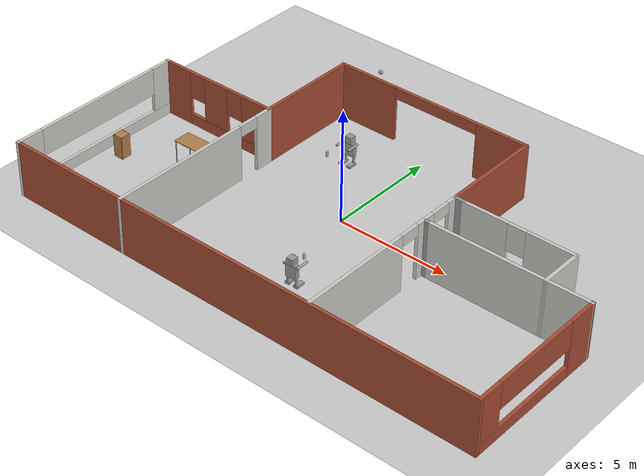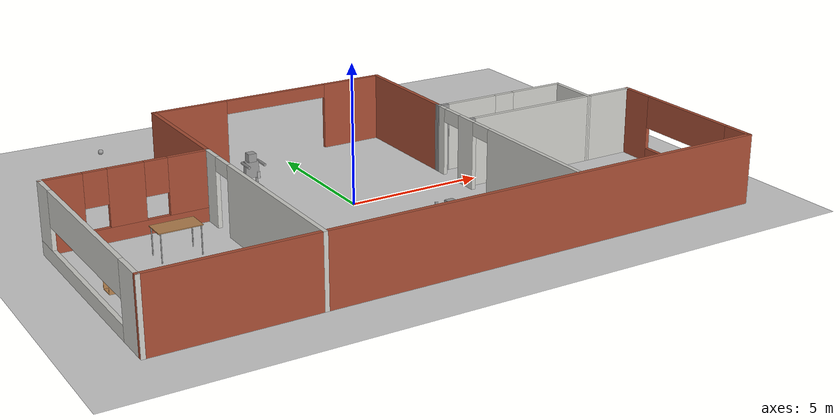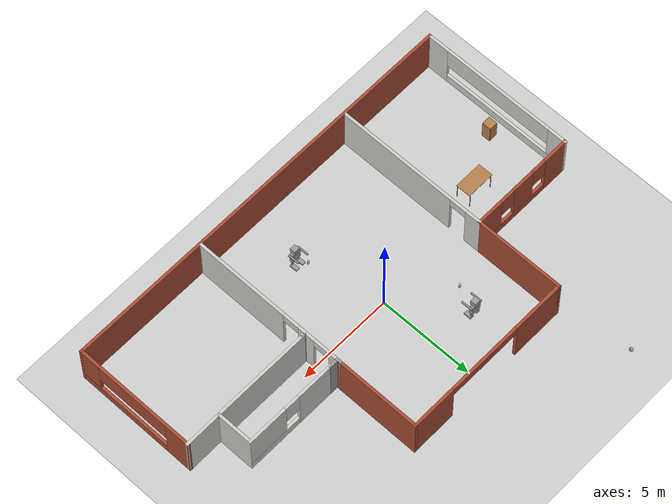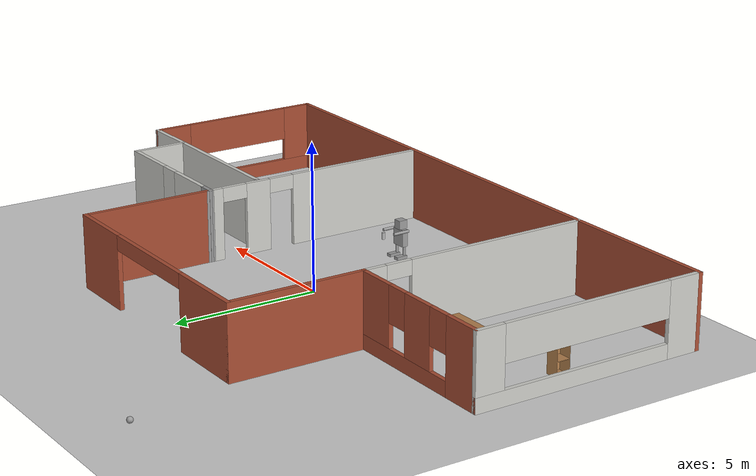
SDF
<sdf version="1.6">
 <world name="default">
  <plugin name="welcome" filename="libwelcome.so"/>
  <light name="sun" type="directional">
   <pose>0 0 10 0 -0 0</pose>
   <diffuse>0.8 0.8 0.8 1</diffuse>
   <specular>0.2 0.2 0.2 1</specular>
   <attenuation>
    <range>1000</range>
    <constant>0.9</constant>
    <linear>0.01</linear>
    <quadratic>0.001</quadratic>
   </attenuation>
   <direction>-0.5 0.1 -0.9</direction>
  </light>
  <model name="ground_plane">
   <static>1</static>
   <link name="link">
    <collision name="collision">
     <geometry><plane><normal>0 0 1</normal><size>100 100</size></plane></geometry>
     <surface><friction><ode><mu>100</mu><mu2>50</mu2></ode></friction></surface>
    </collision>
    <visual name="visual">
     <cast_shadows>0</cast_shadows>
     <geometry><plane><normal>0 0 1</normal><size>100 100</size></plane></geometry>
     <material>
      <script><uri>file://media/materials/scripts/gazebo.material</uri><name>Gazebo/Grey</name></script>
     </material>
    </visual>
   </link>
  </model>
  <gravity>0 0 -9.8</gravity>
  <magnetic_field>6e-06 2.3e-05 -4.2e-05</magnetic_field>
  <atmosphere type="adiabatic"/>
  <physics name="default_physics" default="0" type="ode">
   <max_step_size>0.001</max_step_size>
   <real_time_factor>1</real_time_factor>
   <real_time_update_rate>1000</real_time_update_rate>
  </physics>
  <scene><ambient>0.4 0.4 0.4 1</ambient><background>0.7 0.7 0.7 1</background><shadows>1</shadows></scene>
  <spherical_coordinates>
   <surface_model>EARTH_WGS84</surface_model>
   <latitude_deg>0</latitude_deg>
   <longitude_deg>0</longitude_deg>
   <elevation>0</elevation>
   <heading_deg>0</heading_deg>
  </spherical_coordinates>
  <model name="Building">
   <pose>0.53973 -0.53999 0 0 -0 0</pose>
   <link name="Wall_11">
    <pose>6.62948 1.82989 0 0 -0 0</pose>
    <visual name="Wall_11_Visual_0">
     <pose>-1.4822 0 1.25 0 -0 0</pose>
     <geometry><box><size>2.0356 0.15 2.5</size></box></geometry>
     <material>
      <script><uri>file://media/materials/scripts/gazebo.material</uri><name>Gazebo/CeilingTiled</name></script>
      <ambient>0.435294 0.796078 0.67451 1</ambient>
     </material>
     <meta><layer>0</layer></meta>
    </visual>
    <collision name="Wall_11_Collision_0">
     <geometry><box><size>2.0356 0.15 2.5</size></box></geometry>
     <pose>-1.4822 0 1.25 0 -0 0</pose>
    </collision>
    <visual name="Wall_11_Visual_1">
     <pose>1.0178 0 0.25 0 -0 0</pose>
     <geometry><box><size>2.9644 0.15 0.5</size></box></geometry>
     <material>
      <script><uri>file://media/materials/scripts/gazebo.material</uri><name>Gazebo/CeilingTiled</name></script>
      <ambient>0.435294 0.796078 0.67451 1</ambient>
     </material>
     <meta><layer>0</layer></meta>
    </visual>
    <collision name="Wall_11_Collision_1">
     <geometry><box><size>2.9644 0.15 0.5</size></box></geometry>
     <pose>1.0178 0 0.25 0 -0 0</pose>
    </collision>
    <visual name="Wall_11_Visual_2">
     <pose>1.4178 0 1.5 0 -0 0</pose>
     <geometry><box><size>2.1644 0.15 2</size></box></geometry>
     <material>
      <script><uri>file://media/materials/scripts/gazebo.material</uri><name>Gazebo/CeilingTiled</name></script>
      <ambient>0.435294 0.796078 0.67451 1</ambient>
     </material>
     <meta><layer>0</layer></meta>
    </visual>
    <collision name="Wall_11_Collision_2">
     <geometry><box><size>2.1644 0.15 2</size></box></geometry>
     <pose>1.4178 0 1.5 0 -0 0</pose>
    </collision>
    <visual name="Wall_11_Visual_3">
     <pose>-0.064396 0 1.9 0 -0 0</pose>
     <geometry><box><size>0.8 0.15 1.2</size></box></geometry>
     <material>
      <script><uri>file://media/materials/scripts/gazebo.material</uri><name>Gazebo/CeilingTiled</name></script>
      <ambient>0.435294 0.796078 0.67451 1</ambient>
     </material>
     <meta><layer>0</layer></meta>
    </visual>
    <collision name="Wall_11_Collision_3">
     <geometry><box><size>0.8 0.15 1.2</size></box></geometry>
     <pose>-0.064396 0 1.9 0 -0 0</pose>
    </collision>
   </link>
   <link name="Wall_12">
    <collision name="Wall_12_Collision">
     <geometry><box><size>2 0.15 2.5</size></box></geometry>
     <pose>0 0 1.25 0 -0 0</pose>
    </collision>
    <visual name="Wall_12_Visual">
     <pose>0 0 1.25 0 -0 0</pose>
     <geometry><box><size>2 0.15 2.5</size></box></geometry>
     <material>
      <script><uri>file://media/materials/scripts/gazebo.material</uri><name>Gazebo/CeilingTiled</name></script>
      <ambient>0.435294 0.796078 0.67451 1</ambient>
     </material>
     <meta><layer>0</layer></meta>
    </visual>
    <pose>9.05449 0.904887 0 0 0 -1.5708</pose>
   </link>
   <link name="Wall_13">
    <collision name="Wall_13_Collision">
     <geometry><box><size>2.02022 0.15 2.5</size></box></geometry>
     <pose>0 0 1.25 0 -0 0</pose>
    </collision>
    <visual name="Wall_13_Visual">
     <pose>0 0 1.25 0 -0 0</pose>
     <geometry><box><size>2.02022 0.15 2.5</size></box></geometry>
     <material>
      <script><uri>file://media/materials/scripts/gazebo.material</uri><name>Gazebo/CeilingTiled</name></script>
      <ambient>1 1 1 1</ambient>
     </material>
     <meta><layer>0</layer></meta>
    </visual>
    <pose>9.98954 -0.010056 0 0 -0 0.010755</pose>
   </link>
   <link name="Wall_14">
    <pose>10.9246 -3.175 0 0 0 -1.5708</pose>
    <visual name="Wall_14_Visual_0">
     <pose>-2.57463 0 1.25 0 -0 0</pose>
     <geometry><box><size>1.35073 0.15 2.5</size></box></geometry>
     <material>
      <script><uri>file://media/materials/scripts/gazebo.material</uri><name>Gazebo/Bricks</name></script>
      <ambient>1 1 1 1</ambient>
     </material>
     <meta><layer>0</layer></meta>
    </visual>
    <collision name="Wall_14_Collision_0">
     <geometry><box><size>1.35073 0.15 2.5</size></box></geometry>
     <pose>-2.57463 0 1.25 0 -0 0</pose>
    </collision>
    <visual name="Wall_14_Visual_1">
     <pose>0.675366 0 0.25 0 -0 0</pose>
     <geometry><box><size>5.14927 0.15 0.5</size></box></geometry>
     <material>
      <script><uri>file://media/materials/scripts/gazebo.material</uri><name>Gazebo/Bricks</name></script>
      <ambient>1 1 1 1</ambient>
     </material>
     <meta><layer>0</layer></meta>
    </visual>
    <collision name="Wall_14_Collision_1">
     <geometry><box><size>5.14927 0.15 0.5</size></box></geometry>
     <pose>0.675366 0 0.25 0 -0 0</pose>
    </collision>
    <visual name="Wall_14_Visual_2">
     <pose>2.67537 0 1.5 0 -0 0</pose>
     <geometry><box><size>1.14927 0.15 2</size></box></geometry>
     <material>
      <script><uri>file://media/materials/scripts/gazebo.material</uri><name>Gazebo/Bricks</name></script>
      <ambient>1 1 1 1</ambient>
     </material>
     <meta><layer>0</layer></meta>
    </visual>
    <collision name="Wall_14_Collision_2">
     <geometry><box><size>1.14927 0.15 2</size></box></geometry>
     <pose>2.67537 0 1.5 0 -0 0</pose>
    </collision>
    <visual name="Wall_14_Visual_3">
     <pose>0.100732 0 1.9 0 -0 0</pose>
     <geometry><box><size>4 0.15 1.2</size></box></geometry>
     <material>
      <script><uri>file://media/materials/scripts/gazebo.material</uri><name>Gazebo/Bricks</name></script>
      <ambient>1 1 1 1</ambient>
     </material>
     <meta><layer>0</layer></meta>
    </visual>
    <collision name="Wall_14_Collision_3">
     <geometry><box><size>4 0.15 1.2</size></box></geometry>
     <pose>0.100732 0 1.9 0 -0 0</pose>
    </collision>
   </link>
   <link name="Wall_15">
    <collision name="Wall_15_Collision">
     <geometry><box><size>22 0.15 2.5</size></box></geometry>
     <pose>0 0 1.25 0 -0 0</pose>
    </collision>
    <visual name="Wall_15_Visual">
     <pose>0 0 1.25 0 -0 0</pose>
     <geometry><box><size>22 0.15 2.5</size></box></geometry>
     <material>
      <script><uri>file://media/materials/scripts/gazebo.material</uri><name>Gazebo/Bricks</name></script>
      <ambient>1 1 1 1</ambient>
     </material>
     <meta><layer>0</layer></meta>
    </visual>
    <pose>-0.000401 -6.35 0 0 -0 3.14159</pose>
   </link>
   <link name="Wall_16">
    <pose>-10.9254 -2.3 0 0 -0 1.5708</pose>
    <visual name="Wall_16_Visual_0">
     <pose>-3.50481 0 1.25 0 -0 0</pose>
     <geometry><box><size>1.24037 0.15 2.5</size></box></geometry>
     <material>
      <script><uri>file://media/materials/scripts/gazebo.material</uri><name>Gazebo/CeilingTiled</name></script>
      <ambient>0.435294 0.796078 0.67451 1</ambient>
     </material>
     <meta><layer>0</layer></meta>
    </visual>
    <collision name="Wall_16_Collision_0">
     <geometry><box><size>1.24037 0.15 2.5</size></box></geometry>
     <pose>-3.50481 0 1.25 0 -0 0</pose>
    </collision>
    <visual name="Wall_16_Visual_1">
     <pose>0.620185 0 0.25 0 -0 0</pose>
     <geometry><box><size>7.00963 0.15 0.5</size></box></geometry>
     <material>
      <script><uri>file://media/materials/scripts/gazebo.material</uri><name>Gazebo/CeilingTiled</name></script>
      <ambient>0.435294 0.796078 0.67451 1</ambient>
     </material>
     <meta><layer>0</layer></meta>
    </visual>
    <collision name="Wall_16_Collision_1">
     <geometry><box><size>7.00963 0.15 0.5</size></box></geometry>
     <pose>0.620185 0 0.25 0 -0 0</pose>
    </collision>
    <visual name="Wall_16_Visual_2">
     <pose>3.62019 0 1.5 0 -0 0</pose>
     <geometry><box><size>1.00963 0.15 2</size></box></geometry>
     <material>
      <script><uri>file://media/materials/scripts/gazebo.material</uri><name>Gazebo/CeilingTiled</name></script>
      <ambient>0.435294 0.796078 0.67451 1</ambient>
     </material>
     <meta><layer>0</layer></meta>
    </visual>
    <collision name="Wall_16_Collision_2">
     <geometry><box><size>1.00963 0.15 2</size></box></geometry>
     <pose>3.62019 0 1.5 0 -0 0</pose>
    </collision>
    <visual name="Wall_16_Visual_3">
     <pose>0.11537 0 1.9 0 -0 0</pose>
     <geometry><box><size>6 0.15 1.2</size></box></geometry>
     <material>
      <script><uri>file://media/materials/scripts/gazebo.material</uri><name>Gazebo/CeilingTiled</name></script>
      <ambient>0.435294 0.796078 0.67451 1</ambient>
     </material>
     <meta><layer>0</layer></meta>
    </visual>
    <collision name="Wall_16_Collision_3">
     <geometry><box><size>6 0.15 1.2</size></box></geometry>
     <pose>0.11537 0 1.9 0 -0 0</pose>
    </collision>
   </link>
   <link name="Wall_17">
    <pose>-8.1254 1.75 0 0 -0 0</pose>
    <visual name="Wall_17_Visual_0">
     <pose>-2.16717 0 1.25 0 -0 0</pose>
     <geometry><box><size>1.41566 0.15 2.5</size></box></geometry>
     <material>
      <script><uri>file://media/materials/scripts/gazebo.material</uri><name>Gazebo/Bricks</name></script>
      <ambient>1 1 1 1</ambient>
     </material>
     <meta><layer>0</layer></meta>
    </visual>
    <collision name="Wall_17_Collision_0">
     <geometry><box><size>1.41566 0.15 2.5</size></box></geometry>
     <pose>-2.16717 0 1.25 0 -0 0</pose>
    </collision>
    <visual name="Wall_17_Visual_1">
     <pose>0.707832 0 0.25 0 -0 0</pose>
     <geometry><box><size>4.33434 0.15 0.5</size></box></geometry>
     <material>
      <script><uri>file://media/materials/scripts/gazebo.material</uri><name>Gazebo/Bricks</name></script>
      <ambient>1 1 1 1</ambient>
     </material>
     <meta><layer>0</layer></meta>
    </visual>
    <collision name="Wall_17_Collision_1">
     <geometry><box><size>4.33434 0.15 0.5</size></box></geometry>
     <pose>0.707832 0 0.25 0 -0 0</pose>
    </collision>
    <visual name="Wall_17_Visual_2">
     <pose>-0.039392 0 1.5 0 -0 0</pose>
     <geometry><box><size>1.23989 0.15 2</size></box></geometry>
     <material>
      <script><uri>file://media/materials/scripts/gazebo.material</uri><name>Gazebo/Bricks</name></script>
      <ambient>1 1 1 1</ambient>
     </material>
     <meta><layer>0</layer></meta>
    </visual>
    <collision name="Wall_17_Collision_2">
     <geometry><box><size>1.23989 0.15 2</size></box></geometry>
     <pose>-0.039392 0 1.5 0 -0 0</pose>
    </collision>
    <visual name="Wall_17_Visual_3">
     <pose>2.12778 0 1.5 0 -0 0</pose>
     <geometry><box><size>1.49445 0.15 2</size></box></geometry>
     <material>
      <script><uri>file://media/materials/scripts/gazebo.material</uri><name>Gazebo/Bricks</name></script>
      <ambient>1 1 1 1</ambient>
     </material>
     <meta><layer>0</layer></meta>
    </visual>
    <collision name="Wall_17_Collision_3">
     <geometry><box><size>1.49445 0.15 2</size></box></geometry>
     <pose>2.12778 0 1.5 0 -0 0</pose>
    </collision>
    <visual name="Wall_17_Visual_4">
     <pose>-1.05934 0 1.9 0 -0 0</pose>
     <geometry><box><size>0.8 0.15 1.2</size></box></geometry>
     <material>
      <script><uri>file://media/materials/scripts/gazebo.material</uri><name>Gazebo/Bricks</name></script>
      <ambient>1 1 1 1</ambient>
     </material>
     <meta><layer>0</layer></meta>
    </visual>
    <collision name="Wall_17_Collision_4">
     <geometry><box><size>0.8 0.15 1.2</size></box></geometry>
     <pose>-1.05934 0 1.9 0 -0 0</pose>
    </collision>
    <visual name="Wall_17_Visual_5">
     <pose>0.980551 0 1.9 0 -0 0</pose>
     <geometry><box><size>0.8 0.15 1.2</size></box></geometry>
     <material>
      <script><uri>file://media/materials/scripts/gazebo.material</uri><name>Gazebo/Bricks</name></script>
      <ambient>1 1 1 1</ambient>
     </material>
     <meta><layer>0</layer></meta>
    </visual>
    <collision name="Wall_17_Collision_5">
     <geometry><box><size>0.8 0.15 1.2</size></box></geometry>
     <pose>0.980551 0 1.9 0 -0 0</pose>
    </collision>
   </link>
   <link name="Wall_18">
    <collision name="Wall_18_Collision">
     <geometry><box><size>4.75 0.15 2.5</size></box></geometry>
     <pose>0 0 1.25 0 -0 0</pose>
    </collision>
    <visual name="Wall_18_Visual">
     <pose>0 0 1.25 0 -0 0</pose>
     <geometry><box><size>4.75 0.15 2.5</size></box></geometry>
     <material>
      <script><uri>file://media/materials/scripts/gazebo.material</uri><name>Gazebo/Bricks</name></script>
      <ambient>1 1 1 1</ambient>
     </material>
     <meta><layer>0</layer></meta>
    </visual>
    <pose>-5.3254 4.05 0 0 -0 1.5708</pose>
   </link>
   <link name="Wall_19">
    <pose>-0.775401 6.35 0 0 -0 0</pose>
    <visual name="Wall_19_Visual_0">
     <pose>-3.2002 0 1.25 0 -0 0</pose>
     <geometry><box><size>2.8496 0.15 2.5</size></box></geometry>
     <material>
      <script><uri>file://media/materials/scripts/gazebo.material</uri><name>Gazebo/Bricks</name></script>
      <ambient>1 1 1 1</ambient>
     </material>
     <meta><layer>0</layer></meta>
    </visual>
    <collision name="Wall_19_Collision_0">
     <geometry><box><size>2.8496 0.15 2.5</size></box></geometry>
     <pose>-3.2002 0 1.25 0 -0 0</pose>
    </collision>
    <visual name="Wall_19_Visual_1">
     <pose>3.4248 0 1.25 0 -0 0</pose>
     <geometry><box><size>2.4004 0.15 2.5</size></box></geometry>
     <material>
      <script><uri>file://media/materials/scripts/gazebo.material</uri><name>Gazebo/Bricks</name></script>
      <ambient>1 1 1 1</ambient>
     </material>
     <meta><layer>0</layer></meta>
    </visual>
    <collision name="Wall_19_Collision_1">
     <geometry><box><size>2.4004 0.15 2.5</size></box></geometry>
     <pose>3.4248 0 1.25 0 -0 0</pose>
    </collision>
    <visual name="Wall_19_Visual_2">
     <pose>0.224605 0 2.25 0 -0 0</pose>
     <geometry><box><size>4 0.15 0.5</size></box></geometry>
     <material>
      <script><uri>file://media/materials/scripts/gazebo.material</uri><name>Gazebo/Bricks</name></script>
      <ambient>1 1 1 1</ambient>
     </material>
     <meta><layer>0</layer></meta>
    </visual>
    <collision name="Wall_19_Collision_2">
     <geometry><box><size>4 0.15 0.5</size></box></geometry>
     <pose>0.224605 0 2.25 0 -0 0</pose>
    </collision>
   </link>
   <link name="Wall_20">
    <collision name="Wall_20_Collision">
     <geometry><box><size>4.5 0.15 2.5</size></box></geometry>
     <pose>0 0 1.25 0 -0 0</pose>
    </collision>
    <visual name="Wall_20_Visual">
     <pose>0 0 1.25 0 -0 0</pose>
     <geometry><box><size>4.5 0.15 2.5</size></box></geometry>
     <material>
      <script><uri>file://media/materials/scripts/gazebo.material</uri><name>Gazebo/Bricks</name></script>
      <ambient>1 1 1 1</ambient>
     </material>
     <meta><layer>0</layer></meta>
    </visual>
    <pose>3.7746 4.175 0 0 0 -1.5708</pose>
   </link>
   <link name="Wall_23">
    <collision name="Wall_23_Collision">
     <geometry><box><size>0.323879 0.15 2.5</size></box></geometry>
     <pose>0 0 1.25 0 -0 0</pose>
    </collision>
    <visual name="Wall_23_Visual">
     <pose>0 0 1.25 0 -0 0</pose>
     <geometry><box><size>0.323879 0.15 2.5</size></box></geometry>
     <material>
      <script><uri>file://media/materials/scripts/gazebo.material</uri><name>Gazebo/Grey</name></script>
      <ambient>1 1 1 1</ambient>
     </material>
     <meta><layer>0</layer></meta>
    </visual>
    <pose>3.77125 1.91312 0 0 0 -1.60936</pose>
   </link>
   <link name="Wall_26">
    <collision name="Wall_26_Collision">
     <geometry><box><size>0.587206 0.15 2.5</size></box></geometry>
     <pose>0 0 1.25 0 -0 0</pose>
    </collision>
    <visual name="Wall_26_Visual">
     <pose>0 0 1.25 0 -0 0</pose>
     <geometry><box><size>0.587206 0.15 2.5</size></box></geometry>
     <material>
      <script><uri>file://media/materials/scripts/gazebo.material</uri><name>Gazebo/Grey</name></script>
      <ambient>1 1 1 1</ambient>
     </material>
     <meta><layer>0</layer></meta>
    </visual>
    <pose>3.98619 1.83477 0 0 0 -3.13326</pose>
   </link>
   <link name="Wall_28">
    <pose>-5.3254 -2.3 0 0 0 -1.5708</pose>
    <visual name="Wall_28_Visual_0">
     <pose>-3.6972 0 1.25 0 -0 0</pose>
     <geometry><box><size>0.855593 0.15 2.5</size></box></geometry>
     <material>
      <script><uri>file://media/materials/scripts/gazebo.material</uri><name>Gazebo/CeilingTiled</name></script>
      <ambient>0.996078 0.47451 0.0196078 1</ambient>
     </material>
     <meta><layer>0</layer></meta>
    </visual>
    <collision name="Wall_28_Collision_0">
     <geometry><box><size>0.855593 0.15 2.5</size></box></geometry>
     <pose>-3.6972 0 1.25 0 -0 0</pose>
    </collision>
    <visual name="Wall_28_Visual_1">
     <pose>0.877797 0 1.25 0 -0 0</pose>
     <geometry><box><size>6.49441 0.15 2.5</size></box></geometry>
     <material>
      <script><uri>file://media/materials/scripts/gazebo.material</uri><name>Gazebo/CeilingTiled</name></script>
      <ambient>0.996078 0.47451 0.0196078 1</ambient>
     </material>
     <meta><layer>0</layer></meta>
    </visual>
    <collision name="Wall_28_Collision_1">
     <geometry><box><size>6.49441 0.15 2.5</size></box></geometry>
     <pose>0.877797 0 1.25 0 -0 0</pose>
    </collision>
    <visual name="Wall_28_Visual_2">
     <pose>-2.81941 0 2.25 0 -0 0</pose>
     <geometry><box><size>0.9 0.15 0.5</size></box></geometry>
     <material>
      <script><uri>file://media/materials/scripts/gazebo.material</uri><name>Gazebo/CeilingTiled</name></script>
      <ambient>0.996078 0.47451 0.0196078 1</ambient>
     </material>
     <meta><layer>0</layer></meta>
    </visual>
    <collision name="Wall_28_Collision_2">
     <geometry><box><size>0.9 0.15 0.5</size></box></geometry>
     <pose>-2.81941 0 2.25 0 -0 0</pose>
    </collision>
   </link>
   <link name="Wall_30">
    <pose>3.7679 -2.21705 0 0 0 -1.5708</pose>
    <visual name="Wall_30_Visual_0">
     <pose>-3.8692 0 1.25 0 -0 0</pose>
     <geometry><box><size>0.511595 0.15 2.5</size></box></geometry>
     <material>
      <script><uri>file://media/materials/scripts/gazebo.material</uri><name>Gazebo/CeilingTiled</name></script>
      <ambient>0.996078 0.47451 0.0196078 1</ambient>
     </material>
     <meta><layer>0</layer></meta>
    </visual>
    <collision name="Wall_30_Collision_0">
     <geometry><box><size>0.511595 0.15 2.5</size></box></geometry>
     <pose>-3.8692 0 1.25 0 -0 0</pose>
    </collision>
    <visual name="Wall_30_Visual_1">
     <pose>-2.26206 0 1.25 0 -0 0</pose>
     <geometry><box><size>0.902691 0.15 2.5</size></box></geometry>
     <material>
      <script><uri>file://media/materials/scripts/gazebo.material</uri><name>Gazebo/CeilingTiled</name></script>
      <ambient>0.996078 0.47451 0.0196078 1</ambient>
     </material>
     <meta><layer>0</layer></meta>
    </visual>
    <collision name="Wall_30_Collision_1">
     <geometry><box><size>0.902691 0.15 2.5</size></box></geometry>
     <pose>-2.26206 0 1.25 0 -0 0</pose>
    </collision>
    <visual name="Wall_30_Visual_2">
     <pose>1.60714 0 1.25 0 -0 0</pose>
     <geometry><box><size>5.03571 0.15 2.5</size></box></geometry>
     <material>
      <script><uri>file://media/materials/scripts/gazebo.material</uri><name>Gazebo/CeilingTiled</name></script>
      <ambient>0.996078 0.47451 0.0196078 1</ambient>
     </material>
     <meta><layer>0</layer></meta>
    </visual>
    <collision name="Wall_30_Collision_2">
     <geometry><box><size>5.03571 0.15 2.5</size></box></geometry>
     <pose>1.60714 0 1.25 0 -0 0</pose>
    </collision>
    <visual name="Wall_30_Visual_3">
     <pose>-3.16341 0 2.25 0 -0 0</pose>
     <geometry><box><size>0.9 0.15 0.5</size></box></geometry>
     <material>
      <script><uri>file://media/materials/scripts/gazebo.material</uri><name>Gazebo/CeilingTiled</name></script>
      <ambient>0.996078 0.47451 0.0196078 1</ambient>
     </material>
     <meta><layer>0</layer></meta>
    </visual>
    <collision name="Wall_30_Collision_3">
     <geometry><box><size>0.9 0.15 0.5</size></box></geometry>
     <pose>-3.16341 0 2.25 0 -0 0</pose>
    </collision>
    <visual name="Wall_30_Visual_4">
     <pose>-1.36071 0 2.25 0 -0 0</pose>
     <geometry><box><size>0.9 0.15 0.5</size></box></geometry>
     <material>
      <script><uri>file://media/materials/scripts/gazebo.material</uri><name>Gazebo/CeilingTiled</name></script>
      <ambient>0.996078 0.47451 0.0196078 1</ambient>
     </material>
     <meta><layer>0</layer></meta>
    </visual>
    <collision name="Wall_30_Collision_4">
     <geometry><box><size>0.9 0.15 0.5</size></box></geometry>
     <pose>-1.36071 0 2.25 0 -0 0</pose>
    </collision>
   </link>
   <link name="Wall_34">
    <collision name="Wall_34_Collision">
     <geometry><box><size>5.25 0.15 2.5</size></box></geometry>
     <pose>0 0 1.25 0 -0 0</pose>
    </collision>
    <visual name="Wall_34_Visual">
     <pose>0 0 1.25 0 -0 0</pose>
     <geometry><box><size>5.25 0.15 2.5</size></box></geometry>
     <material>
      <script><uri>file://media/materials/scripts/gazebo.material</uri><name>Gazebo/CeilingTiled</name></script>
      <ambient>0.996078 0.47451 0.0196078 1</ambient>
     </material>
     <meta><layer>0</layer></meta>
    </visual>
    <pose>6.50448 -0.020113 0 0 -0 3.14159</pose>
   </link>
   <link name="Wall_35">
    <collision name="Wall_35_Collision">
     <geometry><box><size>0.25 0.15 2.5</size></box></geometry>
     <pose>0 0 1.25 0 -0 0</pose>
    </collision>
    <visual name="Wall_35_Visual">
     <pose>0 0 1.25 0 -0 0</pose>
     <geometry><box><size>0.25 0.15 2.5</size></box></geometry>
     <material>
      <script><uri>file://media/materials/scripts/gazebo.material</uri><name>Gazebo/Grey</name></script>
      <ambient>1 1 1 1</ambient>
     </material>
     <meta><layer>0</layer></meta>
    </visual>
    <pose>3.90449 -0.020113 0 0 -0 3.14159</pose>
   </link>
   <static>1</static>
  </model>
  <model name="Robot">
   <link name="link_0_clone">
    <pose>0.4 0.150001 0.299999 -2e-05 0 0</pose>
    <inertial>
     <mass>1</mass>
     <inertia><ixx>0.145833</ixx><ixy>0</ixy><ixz>0</ixz><iyy>0.145833</iyy><iyz>0</iyz><izz>0.125</izz></inertia>
    </inertial>
    <visual name="visual">
     <geometry><cylinder><radius>0.05</radius><length>0.3</length></cylinder></geometry>
     <material>
      <lighting>1</lighting>
      <script><uri>file://media/materials/scripts/gazebo.material</uri><name>Gazebo/Grey</name></script>
      <shader type="pixel"><normal_map>__default__</normal_map></shader>
      <ambient>0.3 0.3 0.3 1</ambient>
      <diffuse>0.7 0.7 0.7 1</diffuse>
      <specular>0.01 0.01 0.01 1</specular>
      <emissive>0 0 0 1</emissive>
     </material>
    </visual>
    <collision name="collision">
     <geometry><cylinder><radius>0.05</radius><length>0.3</length></cylinder></geometry>
     <surface>
      <friction>
       <ode><mu>1</mu><mu2>1</mu2><fdir1>0 0 0</fdir1><slip1>0</slip1><slip2>0</slip2></ode>
       <torsional>
        <coefficient>1</coefficient>
        <patch_radius>0</patch_radius>
        <surface_radius>0</surface_radius>
        <use_patch_radius>1</use_patch_radius>
        <ode><slip>0</slip></ode>
       </torsional>
      </friction>
      <bounce><restitution_coefficient>0</restitution_coefficient><threshold>1e+06</threshold></bounce>
      <contact>
       <collide_without_contact>0</collide_without_contact>
       <collide_without_contact_bitmask>1</collide_without_contact_bitmask>
       <collide_bitmask>1</collide_bitmask>
       <ode>
        <soft_cfm>0</soft_cfm>
        <soft_erp>0.2</soft_erp>
        <kp>1e+13</kp>
        <kd>1</kd>
        <max_vel>0.01</max_vel>
        <min_depth>0</min_depth>
       </ode>
       <bullet>
        <split_impulse>1</split_impulse>
        <split_impulse_penetration_threshold>-0.01</split_impulse_penetration_threshold>
        <soft_cfm>0</soft_cfm>
        <soft_erp>0.2</soft_erp>
        <kp>1e+13</kp>
        <kd>1</kd>
       </bullet>
      </contact>
     </surface>
    </collision>
   </link>
   <link name="link_0_clone_clone">
    <pose>0 0.149999 0.3 -3e-05 -0 -0</pose>
    <inertial>
     <mass>1</mass>
     <inertia><ixx>0.145833</ixx><ixy>0</ixy><ixz>0</ixz><iyy>0.145833</iyy><iyz>0</iyz><izz>0.125</izz></inertia>
    </inertial>
    <visual name="visual">
     <geometry><cylinder><radius>0.05</radius><length>0.3</length></cylinder></geometry>
     <material>
      <lighting>1</lighting>
      <script><uri>file://media/materials/scripts/gazebo.material</uri><name>Gazebo/Grey</name></script>
      <shader type="pixel"><normal_map>__default__</normal_map></shader>
      <ambient>0.3 0.3 0.3 1</ambient>
      <diffuse>0.7 0.7 0.7 1</diffuse>
      <specular>0.01 0.01 0.01 1</specular>
      <emissive>0 0 0 1</emissive>
     </material>
    </visual>
    <collision name="collision">
     <geometry><cylinder><radius>0.05</radius><length>0.3</length></cylinder></geometry>
     <surface>
      <friction>
       <ode><mu>1</mu><mu2>1</mu2><fdir1>0 0 0</fdir1><slip1>0</slip1><slip2>0</slip2></ode>
       <torsional>
        <coefficient>1</coefficient>
        <patch_radius>0</patch_radius>
        <surface_radius>0</surface_radius>
        <use_patch_radius>1</use_patch_radius>
        <ode><slip>0</slip></ode>
       </torsional>
      </friction>
      <bounce><restitution_coefficient>0</restitution_coefficient><threshold>1e+06</threshold></bounce>
      <contact>
       <collide_without_contact>0</collide_without_contact>
       <collide_without_contact_bitmask>1</collide_without_contact_bitmask>
       <collide_bitmask>1</collide_bitmask>
       <ode>
        <soft_cfm>0</soft_cfm>
        <soft_erp>0.2</soft_erp>
        <kp>1e+13</kp>
        <kd>1</kd>
        <max_vel>0.01</max_vel>
        <min_depth>0</min_depth>
       </ode>
       <bullet>
        <split_impulse>1</split_impulse>
        <split_impulse_penetration_threshold>-0.01</split_impulse_penetration_threshold>
        <soft_cfm>0</soft_cfm>
        <soft_erp>0.2</soft_erp>
        <kp>1e+13</kp>
        <kd>1</kd>
       </bullet>
      </contact>
     </surface>
    </collision>
   </link>
   <link name="link_0_clone_clone_0">
    <pose>-0.1 -0.049994 0.999978 1.5707 -0 0</pose>
    <inertial>
     <mass>1</mass>
     <inertia><ixx>0.145833</ixx><ixy>0</ixy><ixz>0</ixz><iyy>0.145833</iyy><iyz>0</iyz><izz>0.125</izz></inertia>
    </inertial>
    <visual name="visual">
     <geometry><cylinder><radius>0.05</radius><length>0.6</length></cylinder></geometry>
     <material>
      <lighting>1</lighting>
      <script><uri>file://media/materials/scripts/gazebo.material</uri><name>Gazebo/Grey</name></script>
      <shader type="pixel"><normal_map>__default__</normal_map></shader>
      <ambient>0.3 0.3 0.3 1</ambient>
      <diffuse>0.7 0.7 0.7 1</diffuse>
      <specular>0.01 0.01 0.01 1</specular>
      <emissive>0 0 0 1</emissive>
     </material>
    </visual>
    <collision name="collision">
     <geometry><cylinder><radius>0.05</radius><length>0.6</length></cylinder></geometry>
     <surface>
      <friction>
       <ode><mu>1</mu><mu2>1</mu2><fdir1>0 0 0</fdir1><slip1>0</slip1><slip2>0</slip2></ode>
       <torsional>
        <coefficient>1</coefficient>
        <patch_radius>0</patch_radius>
        <surface_radius>0</surface_radius>
        <use_patch_radius>1</use_patch_radius>
        <ode><slip>0</slip></ode>
       </torsional>
      </friction>
      <bounce><restitution_coefficient>0</restitution_coefficient><threshold>1e+06</threshold></bounce>
      <contact>
       <collide_without_contact>0</collide_without_contact>
       <collide_without_contact_bitmask>1</collide_without_contact_bitmask>
       <collide_bitmask>1</collide_bitmask>
       <ode>
        <soft_cfm>0</soft_cfm>
        <soft_erp>0.2</soft_erp>
        <kp>1e+13</kp>
        <kd>1</kd>
        <max_vel>0.01</max_vel>
        <min_depth>0</min_depth>
       </ode>
       <bullet>
        <split_impulse>1</split_impulse>
        <split_impulse_penetration_threshold>-0.01</split_impulse_penetration_threshold>
        <soft_cfm>0</soft_cfm>
        <soft_erp>0.2</soft_erp>
        <kp>1e+13</kp>
        <kd>1</kd>
       </bullet>
      </contact>
     </surface>
    </collision>
   </link>
   <link name="link_0_clone_clone_0_clone">
    <pose>0.5 -0.049994 0.999978 1.5707 -0 0</pose>
    <inertial>
     <mass>1</mass>
     <inertia><ixx>0.145833</ixx><ixy>0</ixy><ixz>0</ixz><iyy>0.145833</iyy><iyz>0</iyz><izz>0.125</izz></inertia>
    </inertial>
    <visual name="visual">
     <geometry><cylinder><radius>0.05</radius><length>0.6</length></cylinder></geometry>
     <material>
      <lighting>1</lighting>
      <script><uri>file://media/materials/scripts/gazebo.material</uri><name>Gazebo/Grey</name></script>
      <shader type="pixel"><normal_map>__default__</normal_map></shader>
      <ambient>0.3 0.3 0.3 1</ambient>
      <diffuse>0.7 0.7 0.7 1</diffuse>
      <specular>0.01 0.01 0.01 1</specular>
      <emissive>0 0 0 1</emissive>
     </material>
    </visual>
    <collision name="collision">
     <geometry><cylinder><radius>0.05</radius><length>0.6</length></cylinder></geometry>
     <surface>
      <friction>
       <ode><mu>1</mu><mu2>1</mu2><fdir1>0 0 0</fdir1><slip1>0</slip1><slip2>0</slip2></ode>
       <torsional>
        <coefficient>1</coefficient>
        <patch_radius>0</patch_radius>
        <surface_radius>0</surface_radius>
        <use_patch_radius>1</use_patch_radius>
        <ode><slip>0</slip></ode>
       </torsional>
      </friction>
      <bounce><restitution_coefficient>0</restitution_coefficient><threshold>1e+06</threshold></bounce>
      <contact>
       <collide_without_contact>0</collide_without_contact>
       <collide_without_contact_bitmask>1</collide_without_contact_bitmask>
       <collide_bitmask>1</collide_bitmask>
       <ode>
        <soft_cfm>0</soft_cfm>
        <soft_erp>0.2</soft_erp>
        <kp>1e+13</kp>
        <kd>1</kd>
        <max_vel>0.01</max_vel>
        <min_depth>0</min_depth>
       </ode>
       <bullet>
        <split_impulse>1</split_impulse>
        <split_impulse_penetration_threshold>-0.01</split_impulse_penetration_threshold>
        <soft_cfm>0</soft_cfm>
        <soft_erp>0.2</soft_erp>
        <kp>1e+13</kp>
        <kd>1</kd>
       </bullet>
      </contact>
     </surface>
    </collision>
   </link>
   <link name="link_clone">
    <pose>-0 -0 0.1 -1e-05 -0 0</pose>
    <inertial>
     <mass>1</mass>
     <inertia>
      <ixx>0.166667</ixx>
      <ixy>0</ixy>
      <ixz>0</ixz>
      <iyy>0.166667</iyy>
      <iyz>0</iyz>
      <izz>0.166667</izz>
     </inertia>
    </inertial>
    <visual name="visual">
     <geometry><box><size>0.2 0.4 0.1</size></box></geometry>
     <material>
      <script><name>Gazebo/Grey</name><uri>file://media/materials/scripts/gazebo.material</uri></script>
      <shader type="pixel"><normal_map>__default__</normal_map></shader>
      <ambient>0.3 0.3 0.3 1</ambient>
      <diffuse>0.7 0.7 0.7 1</diffuse>
      <specular>0.01 0.01 0.01 1</specular>
      <emissive>0 0 0 1</emissive>
     </material>
    </visual>
    <collision name="collision">
     <geometry><box><size>0.2 0.4 0.1</size></box></geometry>
     <surface>
      <friction>
       <ode><mu>1</mu><mu2>1</mu2><fdir1>0 0 0</fdir1><slip1>0</slip1><slip2>0</slip2></ode>
       <torsional>
        <coefficient>1</coefficient>
        <patch_radius>0</patch_radius>
        <surface_radius>0</surface_radius>
        <use_patch_radius>1</use_patch_radius>
        <ode><slip>0</slip></ode>
       </torsional>
      </friction>
      <bounce><restitution_coefficient>0</restitution_coefficient><threshold>1e+06</threshold></bounce>
      <contact>
       <collide_without_contact>0</collide_without_contact>
       <collide_without_contact_bitmask>1</collide_without_contact_bitmask>
       <collide_bitmask>1</collide_bitmask>
       <ode>
        <soft_cfm>0</soft_cfm>
        <soft_erp>0.2</soft_erp>
        <kp>1e+13</kp>
        <kd>1</kd>
        <max_vel>0.01</max_vel>
        <min_depth>0</min_depth>
       </ode>
       <bullet>
        <split_impulse>1</split_impulse>
        <split_impulse_penetration_threshold>-0.01</split_impulse_penetration_threshold>
        <soft_cfm>0</soft_cfm>
        <soft_erp>0.2</soft_erp>
        <kp>1e+13</kp>
        <kd>1</kd>
       </bullet>
      </contact>
     </surface>
    </collision>
   </link>
   <link name="link_clone_0">
    <pose>0.4 -0 0.1 -1e-05 -0 0</pose>
    <inertial>
     <mass>1</mass>
     <inertia>
      <ixx>0.166667</ixx>
      <ixy>0</ixy>
      <ixz>0</ixz>
      <iyy>0.166667</iyy>
      <iyz>0</iyz>
      <izz>0.166667</izz>
     </inertia>
    </inertial>
    <visual name="visual">
     <geometry><box><size>0.2 0.4 0.1</size></box></geometry>
     <material>
      <script><name>Gazebo/Grey</name><uri>file://media/materials/scripts/gazebo.material</uri></script>
      <shader type="pixel"><normal_map>__default__</normal_map></shader>
      <ambient>0.3 0.3 0.3 1</ambient>
      <diffuse>0.7 0.7 0.7 1</diffuse>
      <specular>0.01 0.01 0.01 1</specular>
      <emissive>0 0 0 1</emissive>
     </material>
    </visual>
    <collision name="collision">
     <geometry><box><size>0.2 0.4 0.1</size></box></geometry>
     <surface>
      <friction>
       <ode><mu>1</mu><mu2>1</mu2><fdir1>0 0 0</fdir1><slip1>0</slip1><slip2>0</slip2></ode>
       <torsional>
        <coefficient>1</coefficient>
        <patch_radius>0</patch_radius>
        <surface_radius>0</surface_radius>
        <use_patch_radius>1</use_patch_radius>
        <ode><slip>0</slip></ode>
       </torsional>
      </friction>
      <bounce><restitution_coefficient>0</restitution_coefficient><threshold>1e+06</threshold></bounce>
      <contact>
       <collide_without_contact>0</collide_without_contact>
       <collide_without_contact_bitmask>1</collide_without_contact_bitmask>
       <collide_bitmask>1</collide_bitmask>
       <ode>
        <soft_cfm>0</soft_cfm>
        <soft_erp>0.2</soft_erp>
        <kp>1e+13</kp>
        <kd>1</kd>
        <max_vel>0.01</max_vel>
        <min_depth>0</min_depth>
       </ode>
       <bullet>
        <split_impulse>1</split_impulse>
        <split_impulse_penetration_threshold>-0.01</split_impulse_penetration_threshold>
        <soft_cfm>0</soft_cfm>
        <soft_erp>0.2</soft_erp>
        <kp>1e+13</kp>
        <kd>1</kd>
       </bullet>
      </contact>
     </surface>
    </collision>
   </link>
   <link name="link_clone_0_clone">
    <pose>0.2 0.150005 0.750001 -2e-05 0 0</pose>
    <inertial>
     <mass>1</mass>
     <inertia>
      <ixx>0.166667</ixx>
      <ixy>0</ixy>
      <ixz>0</ixz>
      <iyy>0.166667</iyy>
      <iyz>0</iyz>
      <izz>0.166667</izz>
     </inertia>
    </inertial>
    <visual name="visual">
     <geometry><box><size>0.5 0.2 0.6</size></box></geometry>
     <material>
      <script><name>Gazebo/Grey</name><uri>file://media/materials/scripts/gazebo.material</uri></script>
      <shader type="pixel"><normal_map>__default__</normal_map></shader>
      <ambient>0.3 0.3 0.3 1</ambient>
      <diffuse>0.7 0.7 0.7 1</diffuse>
      <specular>0.01 0.01 0.01 1</specular>
      <emissive>0 0 0 1</emissive>
     </material>
    </visual>
    <collision name="collision">
     <geometry><box><size>0.5 0.2 0.6</size></box></geometry>
     <surface>
      <friction>
       <ode><mu>1</mu><mu2>1</mu2><fdir1>0 0 0</fdir1><slip1>0</slip1><slip2>0</slip2></ode>
       <torsional>
        <coefficient>1</coefficient>
        <patch_radius>0</patch_radius>
        <surface_radius>0</surface_radius>
        <use_patch_radius>1</use_patch_radius>
        <ode><slip>0</slip></ode>
       </torsional>
      </friction>
      <bounce><restitution_coefficient>0</restitution_coefficient><threshold>1e+06</threshold></bounce>
      <contact>
       <collide_without_contact>0</collide_without_contact>
       <collide_without_contact_bitmask>1</collide_without_contact_bitmask>
       <collide_bitmask>1</collide_bitmask>
       <ode>
        <soft_cfm>0</soft_cfm>
        <soft_erp>0.2</soft_erp>
        <kp>1e+13</kp>
        <kd>1</kd>
        <max_vel>0.01</max_vel>
        <min_depth>0</min_depth>
       </ode>
       <bullet>
        <split_impulse>1</split_impulse>
        <split_impulse_penetration_threshold>-0.01</split_impulse_penetration_threshold>
        <soft_cfm>0</soft_cfm>
        <soft_erp>0.2</soft_erp>
        <kp>1e+13</kp>
        <kd>1</kd>
       </bullet>
      </contact>
     </surface>
    </collision>
   </link>
   <link name="link_clone_0_clone_clone">
    <pose>0.2 0.150009 1.2 -3e-05 -0 -0</pose>
    <inertial>
     <mass>1</mass>
     <inertia>
      <ixx>0.166667</ixx>
      <ixy>0</ixy>
      <ixz>0</ixz>
      <iyy>0.166667</iyy>
      <iyz>0</iyz>
      <izz>0.166667</izz>
     </inertia>
    </inertial>
    <visual name="visual">
     <geometry><box><size>0.3 0.3 0.3</size></box></geometry>
     <material>
      <script><name>Gazebo/Grey</name><uri>file://media/materials/scripts/gazebo.material</uri></script>
      <shader type="pixel"><normal_map>__default__</normal_map></shader>
      <ambient>0.3 0.3 0.3 1</ambient>
      <diffuse>0.7 0.7 0.7 1</diffuse>
      <specular>0.01 0.01 0.01 1</specular>
      <emissive>0 0 0 1</emissive>
     </material>
    </visual>
    <collision name="collision">
     <geometry><box><size>0.3 0.3 0.3</size></box></geometry>
     <surface>
      <friction>
       <ode><mu>1</mu><mu2>1</mu2><fdir1>0 0 0</fdir1><slip1>0</slip1><slip2>0</slip2></ode>
       <torsional>
        <coefficient>1</coefficient>
        <patch_radius>0</patch_radius>
        <surface_radius>0</surface_radius>
        <use_patch_radius>1</use_patch_radius>
        <ode><slip>0</slip></ode>
       </torsional>
      </friction>
      <bounce><restitution_coefficient>0</restitution_coefficient><threshold>1e+06</threshold></bounce>
      <contact>
       <collide_without_contact>0</collide_without_contact>
       <collide_without_contact_bitmask>1</collide_without_contact_bitmask>
       <collide_bitmask>1</collide_bitmask>
       <ode>
        <soft_cfm>0</soft_cfm>
        <soft_erp>0.2</soft_erp>
        <kp>1e+13</kp>
        <kd>1</kd>
        <max_vel>0.01</max_vel>
        <min_depth>0</min_depth>
       </ode>
       <bullet>
        <split_impulse>1</split_impulse>
        <split_impulse_penetration_threshold>-0.01</split_impulse_penetration_threshold>
        <soft_cfm>0</soft_cfm>
        <soft_erp>0.2</soft_erp>
        <kp>1e+13</kp>
        <kd>1</kd>
       </bullet>
      </contact>
     </surface>
    </collision>
   </link>
   <joint name="link_0_clone_JOINT_5" type="fixed">
    <parent>link_0_clone</parent>
    <child>link_clone_0_clone</child>
    <physics>
     <ode><limit><cfm>0</cfm><erp>0.2</erp></limit><suspension><cfm>0</cfm><erp>0.2</erp></suspension></ode>
    </physics>
   </joint>
   <joint name="link_0_clone_clone_JOINT_4" type="fixed">
    <parent>link_0_clone_clone</parent>
    <child>link_clone_0_clone</child>
    <physics>
     <ode><limit><cfm>0</cfm><erp>0.2</erp></limit><suspension><cfm>0</cfm><erp>0.2</erp></suspension></ode>
    </physics>
   </joint>
   <joint name="link_clone_0_JOINT_1" type="fixed">
    <parent>link_clone_0</parent>
    <child>link_0_clone</child>
    <physics>
     <ode><limit><cfm>0</cfm><erp>0.2</erp></limit><suspension><cfm>0</cfm><erp>0.2</erp></suspension></ode>
    </physics>
   </joint>
   <joint name="link_clone_0_clone_JOINT_6" type="fixed">
    <parent>link_clone_0_clone</parent>
    <child>link_clone_0_clone_clone</child>
    <physics>
     <ode><limit><cfm>0</cfm><erp>0.2</erp></limit><suspension><cfm>0</cfm><erp>0.2</erp></suspension></ode>
    </physics>
   </joint>
   <joint name="link_clone_0_clone_JOINT_8" type="fixed">
    <parent>link_clone_0_clone</parent>
    <child>link_0_clone_clone_0_clone</child>
    <physics>
     <ode><limit><cfm>0</cfm><erp>0.2</erp></limit><suspension><cfm>0</cfm><erp>0.2</erp></suspension></ode>
    </physics>
   </joint>
   <joint name="link_clone_0_clone_JOINT_9" type="fixed">
    <parent>link_clone_0_clone</parent>
    <child>link_0_clone_clone_0</child>
    <physics>
     <ode><limit><cfm>0</cfm><erp>0.2</erp></limit><suspension><cfm>0</cfm><erp>0.2</erp></suspension></ode>
    </physics>
   </joint>
   <joint name="link_clone_JOINT_0" type="fixed">
    <parent>link_clone</parent>
    <child>link_0_clone_clone</child>
    <physics>
     <ode><limit><cfm>0</cfm><erp>0.2</erp></limit><suspension><cfm>0</cfm><erp>0.2</erp></suspension></ode>
    </physics>
   </joint>
   <static>0</static>
   <pose>-2.48462 3.12268 -0.049999 8e-06 1e-06 0.000512</pose>
  </model>
  <model name="Robot_0">
   <link name="link_0_clone">
    <pose>0.4 0.150001 0.299999 -2e-05 0 0</pose>
    <inertial>
     <mass>1</mass>
     <inertia><ixx>0.145833</ixx><ixy>0</ixy><ixz>0</ixz><iyy>0.145833</iyy><iyz>0</iyz><izz>0.125</izz></inertia>
    </inertial>
    <visual name="visual">
     <geometry><cylinder><radius>0.05</radius><length>0.3</length></cylinder></geometry>
     <material>
      <lighting>1</lighting>
      <script><uri>file://media/materials/scripts/gazebo.material</uri><name>Gazebo/Grey</name></script>
      <shader type="pixel"><normal_map>__default__</normal_map></shader>
      <ambient>0.3 0.3 0.3 1</ambient>
      <diffuse>0.7 0.7 0.7 1</diffuse>
      <specular>0.01 0.01 0.01 1</specular>
      <emissive>0 0 0 1</emissive>
     </material>
    </visual>
    <collision name="collision">
     <geometry><cylinder><radius>0.05</radius><length>0.3</length></cylinder></geometry>
     <surface>
      <friction>
       <ode><mu>1</mu><mu2>1</mu2><fdir1>0 0 0</fdir1><slip1>0</slip1><slip2>0</slip2></ode>
       <torsional>
        <coefficient>1</coefficient>
        <patch_radius>0</patch_radius>
        <surface_radius>0</surface_radius>
        <use_patch_radius>1</use_patch_radius>
        <ode><slip>0</slip></ode>
       </torsional>
      </friction>
      <bounce><restitution_coefficient>0</restitution_coefficient><threshold>1e+06</threshold></bounce>
      <contact>
       <collide_without_contact>0</collide_without_contact>
       <collide_without_contact_bitmask>1</collide_without_contact_bitmask>
       <collide_bitmask>1</collide_bitmask>
       <ode>
        <soft_cfm>0</soft_cfm>
        <soft_erp>0.2</soft_erp>
        <kp>1e+13</kp>
        <kd>1</kd>
        <max_vel>0.01</max_vel>
        <min_depth>0</min_depth>
       </ode>
       <bullet>
        <split_impulse>1</split_impulse>
        <split_impulse_penetration_threshold>-0.01</split_impulse_penetration_threshold>
        <soft_cfm>0</soft_cfm>
        <soft_erp>0.2</soft_erp>
        <kp>1e+13</kp>
        <kd>1</kd>
       </bullet>
      </contact>
     </surface>
    </collision>
   </link>
   <link name="link_0_clone_clone">
    <pose>0 0.149999 0.3 -3e-05 -0 -0</pose>
    <inertial>
     <mass>1</mass>
     <inertia><ixx>0.145833</ixx><ixy>0</ixy><ixz>0</ixz><iyy>0.145833</iyy><iyz>0</iyz><izz>0.125</izz></inertia>
    </inertial>
    <visual name="visual">
     <geometry><cylinder><radius>0.05</radius><length>0.3</length></cylinder></geometry>
     <material>
      <lighting>1</lighting>
      <script><uri>file://media/materials/scripts/gazebo.material</uri><name>Gazebo/Grey</name></script>
      <shader type="pixel"><normal_map>__default__</normal_map></shader>
      <ambient>0.3 0.3 0.3 1</ambient>
      <diffuse>0.7 0.7 0.7 1</diffuse>
      <specular>0.01 0.01 0.01 1</specular>
      <emissive>0 0 0 1</emissive>
     </material>
    </visual>
    <collision name="collision">
     <geometry><cylinder><radius>0.05</radius><length>0.3</length></cylinder></geometry>
     <surface>
      <friction>
       <ode><mu>1</mu><mu2>1</mu2><fdir1>0 0 0</fdir1><slip1>0</slip1><slip2>0</slip2></ode>
       <torsional>
        <coefficient>1</coefficient>
        <patch_radius>0</patch_radius>
        <surface_radius>0</surface_radius>
        <use_patch_radius>1</use_patch_radius>
        <ode><slip>0</slip></ode>
       </torsional>
      </friction>
      <bounce><restitution_coefficient>0</restitution_coefficient><threshold>1e+06</threshold></bounce>
      <contact>
       <collide_without_contact>0</collide_without_contact>
       <collide_without_contact_bitmask>1</collide_without_contact_bitmask>
       <collide_bitmask>1</collide_bitmask>
       <ode>
        <soft_cfm>0</soft_cfm>
        <soft_erp>0.2</soft_erp>
        <kp>1e+13</kp>
        <kd>1</kd>
        <max_vel>0.01</max_vel>
        <min_depth>0</min_depth>
       </ode>
       <bullet>
        <split_impulse>1</split_impulse>
        <split_impulse_penetration_threshold>-0.01</split_impulse_penetration_threshold>
        <soft_cfm>0</soft_cfm>
        <soft_erp>0.2</soft_erp>
        <kp>1e+13</kp>
        <kd>1</kd>
       </bullet>
      </contact>
     </surface>
    </collision>
   </link>
   <link name="link_0_clone_clone_0">
    <pose>-0.1 -0.049994 0.999978 1.5707 -0 0</pose>
    <inertial>
     <mass>1</mass>
     <inertia><ixx>0.145833</ixx><ixy>0</ixy><ixz>0</ixz><iyy>0.145833</iyy><iyz>0</iyz><izz>0.125</izz></inertia>
    </inertial>
    <visual name="visual">
     <geometry><cylinder><radius>0.05</radius><length>0.6</length></cylinder></geometry>
     <material>
      <lighting>1</lighting>
      <script><uri>file://media/materials/scripts/gazebo.material</uri><name>Gazebo/Grey</name></script>
      <shader type="pixel"><normal_map>__default__</normal_map></shader>
      <ambient>0.3 0.3 0.3 1</ambient>
      <diffuse>0.7 0.7 0.7 1</diffuse>
      <specular>0.01 0.01 0.01 1</specular>
      <emissive>0 0 0 1</emissive>
     </material>
    </visual>
    <collision name="collision">
     <geometry><cylinder><radius>0.05</radius><length>0.6</length></cylinder></geometry>
     <surface>
      <friction>
       <ode><mu>1</mu><mu2>1</mu2><fdir1>0 0 0</fdir1><slip1>0</slip1><slip2>0</slip2></ode>
       <torsional>
        <coefficient>1</coefficient>
        <patch_radius>0</patch_radius>
        <surface_radius>0</surface_radius>
        <use_patch_radius>1</use_patch_radius>
        <ode><slip>0</slip></ode>
       </torsional>
      </friction>
      <bounce><restitution_coefficient>0</restitution_coefficient><threshold>1e+06</threshold></bounce>
      <contact>
       <collide_without_contact>0</collide_without_contact>
       <collide_without_contact_bitmask>1</collide_without_contact_bitmask>
       <collide_bitmask>1</collide_bitmask>
       <ode>
        <soft_cfm>0</soft_cfm>
        <soft_erp>0.2</soft_erp>
        <kp>1e+13</kp>
        <kd>1</kd>
        <max_vel>0.01</max_vel>
        <min_depth>0</min_depth>
       </ode>
       <bullet>
        <split_impulse>1</split_impulse>
        <split_impulse_penetration_threshold>-0.01</split_impulse_penetration_threshold>
        <soft_cfm>0</soft_cfm>
        <soft_erp>0.2</soft_erp>
        <kp>1e+13</kp>
        <kd>1</kd>
       </bullet>
      </contact>
     </surface>
    </collision>
   </link>
   <link name="link_0_clone_clone_0_clone">
    <pose>0.5 -0.049994 0.999978 1.5707 -0 0</pose>
    <inertial>
     <mass>1</mass>
     <inertia><ixx>0.145833</ixx><ixy>0</ixy><ixz>0</ixz><iyy>0.145833</iyy><iyz>0</iyz><izz>0.125</izz></inertia>
    </inertial>
    <visual name="visual">
     <geometry><cylinder><radius>0.05</radius><length>0.6</length></cylinder></geometry>
     <material>
      <lighting>1</lighting>
      <script><uri>file://media/materials/scripts/gazebo.material</uri><name>Gazebo/Grey</name></script>
      <shader type="pixel"><normal_map>__default__</normal_map></shader>
      <ambient>0.3 0.3 0.3 1</ambient>
      <diffuse>0.7 0.7 0.7 1</diffuse>
      <specular>0.01 0.01 0.01 1</specular>
      <emissive>0 0 0 1</emissive>
     </material>
    </visual>
    <collision name="collision">
     <geometry><cylinder><radius>0.05</radius><length>0.6</length></cylinder></geometry>
     <surface>
      <friction>
       <ode><mu>1</mu><mu2>1</mu2><fdir1>0 0 0</fdir1><slip1>0</slip1><slip2>0</slip2></ode>
       <torsional>
        <coefficient>1</coefficient>
        <patch_radius>0</patch_radius>
        <surface_radius>0</surface_radius>
        <use_patch_radius>1</use_patch_radius>
        <ode><slip>0</slip></ode>
       </torsional>
      </friction>
      <bounce><restitution_coefficient>0</restitution_coefficient><threshold>1e+06</threshold></bounce>
      <contact>
       <collide_without_contact>0</collide_without_contact>
       <collide_without_contact_bitmask>1</collide_without_contact_bitmask>
       <collide_bitmask>1</collide_bitmask>
       <ode>
        <soft_cfm>0</soft_cfm>
        <soft_erp>0.2</soft_erp>
        <kp>1e+13</kp>
        <kd>1</kd>
        <max_vel>0.01</max_vel>
        <min_depth>0</min_depth>
       </ode>
       <bullet>
        <split_impulse>1</split_impulse>
        <split_impulse_penetration_threshold>-0.01</split_impulse_penetration_threshold>
        <soft_cfm>0</soft_cfm>
        <soft_erp>0.2</soft_erp>
        <kp>1e+13</kp>
        <kd>1</kd>
       </bullet>
      </contact>
     </surface>
    </collision>
   </link>
   <link name="link_clone">
    <pose>-0 -0 0.1 -1e-05 -0 0</pose>
    <inertial>
     <mass>1</mass>
     <inertia>
      <ixx>0.166667</ixx>
      <ixy>0</ixy>
      <ixz>0</ixz>
      <iyy>0.166667</iyy>
      <iyz>0</iyz>
      <izz>0.166667</izz>
     </inertia>
    </inertial>
    <visual name="visual">
     <geometry><box><size>0.2 0.4 0.1</size></box></geometry>
     <material>
      <script><name>Gazebo/Grey</name><uri>file://media/materials/scripts/gazebo.material</uri></script>
      <shader type="pixel"><normal_map>__default__</normal_map></shader>
      <ambient>0.3 0.3 0.3 1</ambient>
      <diffuse>0.7 0.7 0.7 1</diffuse>
      <specular>0.01 0.01 0.01 1</specular>
      <emissive>0 0 0 1</emissive>
     </material>
    </visual>
    <collision name="collision">
     <geometry><box><size>0.2 0.4 0.1</size></box></geometry>
     <surface>
      <friction>
       <ode><mu>1</mu><mu2>1</mu2><fdir1>0 0 0</fdir1><slip1>0</slip1><slip2>0</slip2></ode>
       <torsional>
        <coefficient>1</coefficient>
        <patch_radius>0</patch_radius>
        <surface_radius>0</surface_radius>
        <use_patch_radius>1</use_patch_radius>
        <ode><slip>0</slip></ode>
       </torsional>
      </friction>
      <bounce><restitution_coefficient>0</restitution_coefficient><threshold>1e+06</threshold></bounce>
      <contact>
       <collide_without_contact>0</collide_without_contact>
       <collide_without_contact_bitmask>1</collide_without_contact_bitmask>
       <collide_bitmask>1</collide_bitmask>
       <ode>
        <soft_cfm>0</soft_cfm>
        <soft_erp>0.2</soft_erp>
        <kp>1e+13</kp>
        <kd>1</kd>
        <max_vel>0.01</max_vel>
        <min_depth>0</min_depth>
       </ode>
       <bullet>
        <split_impulse>1</split_impulse>
        <split_impulse_penetration_threshold>-0.01</split_impulse_penetration_threshold>
        <soft_cfm>0</soft_cfm>
        <soft_erp>0.2</soft_erp>
        <kp>1e+13</kp>
        <kd>1</kd>
       </bullet>
      </contact>
     </surface>
    </collision>
   </link>
   <link name="link_clone_0">
    <pose>0.4 -0 0.1 -1e-05 -0 0</pose>
    <inertial>
     <mass>1</mass>
     <inertia>
      <ixx>0.166667</ixx>
      <ixy>0</ixy>
      <ixz>0</ixz>
      <iyy>0.166667</iyy>
      <iyz>0</iyz>
      <izz>0.166667</izz>
     </inertia>
    </inertial>
    <visual name="visual">
     <geometry><box><size>0.2 0.4 0.1</size></box></geometry>
     <material>
      <script><name>Gazebo/Grey</name><uri>file://media/materials/scripts/gazebo.material</uri></script>
      <shader type="pixel"><normal_map>__default__</normal_map></shader>
      <ambient>0.3 0.3 0.3 1</ambient>
      <diffuse>0.7 0.7 0.7 1</diffuse>
      <specular>0.01 0.01 0.01 1</specular>
      <emissive>0 0 0 1</emissive>
     </material>
    </visual>
    <collision name="collision">
     <geometry><box><size>0.2 0.4 0.1</size></box></geometry>
     <surface>
      <friction>
       <ode><mu>1</mu><mu2>1</mu2><fdir1>0 0 0</fdir1><slip1>0</slip1><slip2>0</slip2></ode>
       <torsional>
        <coefficient>1</coefficient>
        <patch_radius>0</patch_radius>
        <surface_radius>0</surface_radius>
        <use_patch_radius>1</use_patch_radius>
        <ode><slip>0</slip></ode>
       </torsional>
      </friction>
      <bounce><restitution_coefficient>0</restitution_coefficient><threshold>1e+06</threshold></bounce>
      <contact>
       <collide_without_contact>0</collide_without_contact>
       <collide_without_contact_bitmask>1</collide_without_contact_bitmask>
       <collide_bitmask>1</collide_bitmask>
       <ode>
        <soft_cfm>0</soft_cfm>
        <soft_erp>0.2</soft_erp>
        <kp>1e+13</kp>
        <kd>1</kd>
        <max_vel>0.01</max_vel>
        <min_depth>0</min_depth>
       </ode>
       <bullet>
        <split_impulse>1</split_impulse>
        <split_impulse_penetration_threshold>-0.01</split_impulse_penetration_threshold>
        <soft_cfm>0</soft_cfm>
        <soft_erp>0.2</soft_erp>
        <kp>1e+13</kp>
        <kd>1</kd>
       </bullet>
      </contact>
     </surface>
    </collision>
   </link>
   <link name="link_clone_0_clone">
    <pose>0.2 0.150005 0.750001 -2e-05 0 0</pose>
    <inertial>
     <mass>1</mass>
     <inertia>
      <ixx>0.166667</ixx>
      <ixy>0</ixy>
      <ixz>0</ixz>
      <iyy>0.166667</iyy>
      <iyz>0</iyz>
      <izz>0.166667</izz>
     </inertia>
    </inertial>
    <visual name="visual">
     <geometry><box><size>0.5 0.2 0.6</size></box></geometry>
     <material>
      <script><name>Gazebo/Grey</name><uri>file://media/materials/scripts/gazebo.material</uri></script>
      <shader type="pixel"><normal_map>__default__</normal_map></shader>
      <ambient>0.3 0.3 0.3 1</ambient>
      <diffuse>0.7 0.7 0.7 1</diffuse>
      <specular>0.01 0.01 0.01 1</specular>
      <emissive>0 0 0 1</emissive>
     </material>
    </visual>
    <collision name="collision">
     <geometry><box><size>0.5 0.2 0.6</size></box></geometry>
     <surface>
      <friction>
       <ode><mu>1</mu><mu2>1</mu2><fdir1>0 0 0</fdir1><slip1>0</slip1><slip2>0</slip2></ode>
       <torsional>
        <coefficient>1</coefficient>
        <patch_radius>0</patch_radius>
        <surface_radius>0</surface_radius>
        <use_patch_radius>1</use_patch_radius>
        <ode><slip>0</slip></ode>
       </torsional>
      </friction>
      <bounce><restitution_coefficient>0</restitution_coefficient><threshold>1e+06</threshold></bounce>
      <contact>
       <collide_without_contact>0</collide_without_contact>
       <collide_without_contact_bitmask>1</collide_without_contact_bitmask>
       <collide_bitmask>1</collide_bitmask>
       <ode>
        <soft_cfm>0</soft_cfm>
        <soft_erp>0.2</soft_erp>
        <kp>1e+13</kp>
        <kd>1</kd>
        <max_vel>0.01</max_vel>
        <min_depth>0</min_depth>
       </ode>
       <bullet>
        <split_impulse>1</split_impulse>
        <split_impulse_penetration_threshold>-0.01</split_impulse_penetration_threshold>
        <soft_cfm>0</soft_cfm>
        <soft_erp>0.2</soft_erp>
        <kp>1e+13</kp>
        <kd>1</kd>
       </bullet>
      </contact>
     </surface>
    </collision>
   </link>
   <link name="link_clone_0_clone_clone">
    <pose>0.2 0.150009 1.2 -3e-05 -0 -0</pose>
    <inertial>
     <mass>1</mass>
     <inertia>
      <ixx>0.166667</ixx>
      <ixy>0</ixy>
      <ixz>0</ixz>
      <iyy>0.166667</iyy>
      <iyz>0</iyz>
      <izz>0.166667</izz>
     </inertia>
    </inertial>
    <visual name="visual">
     <geometry><box><size>0.3 0.3 0.3</size></box></geometry>
     <material>
      <script><name>Gazebo/Grey</name><uri>file://media/materials/scripts/gazebo.material</uri></script>
      <shader type="pixel"><normal_map>__default__</normal_map></shader>
      <ambient>0.3 0.3 0.3 1</ambient>
      <diffuse>0.7 0.7 0.7 1</diffuse>
      <specular>0.01 0.01 0.01 1</specular>
      <emissive>0 0 0 1</emissive>
     </material>
    </visual>
    <collision name="collision">
     <geometry><box><size>0.3 0.3 0.3</size></box></geometry>
     <surface>
      <friction>
       <ode><mu>1</mu><mu2>1</mu2><fdir1>0 0 0</fdir1><slip1>0</slip1><slip2>0</slip2></ode>
       <torsional>
        <coefficient>1</coefficient>
        <patch_radius>0</patch_radius>
        <surface_radius>0</surface_radius>
        <use_patch_radius>1</use_patch_radius>
        <ode><slip>0</slip></ode>
       </torsional>
      </friction>
      <bounce><restitution_coefficient>0</restitution_coefficient><threshold>1e+06</threshold></bounce>
      <contact>
       <collide_without_contact>0</collide_without_contact>
       <collide_without_contact_bitmask>1</collide_without_contact_bitmask>
       <collide_bitmask>1</collide_bitmask>
       <ode>
        <soft_cfm>0</soft_cfm>
        <soft_erp>0.2</soft_erp>
        <kp>1e+13</kp>
        <kd>1</kd>
        <max_vel>0.01</max_vel>
        <min_depth>0</min_depth>
       </ode>
       <bullet>
        <split_impulse>1</split_impulse>
        <split_impulse_penetration_threshold>-0.01</split_impulse_penetration_threshold>
        <soft_cfm>0</soft_cfm>
        <soft_erp>0.2</soft_erp>
        <kp>1e+13</kp>
        <kd>1</kd>
       </bullet>
      </contact>
     </surface>
    </collision>
   </link>
   <joint name="link_0_clone_JOINT_5" type="fixed">
    <parent>link_0_clone</parent>
    <child>link_clone_0_clone</child>
    <physics>
     <ode><limit><cfm>0</cfm><erp>0.2</erp></limit><suspension><cfm>0</cfm><erp>0.2</erp></suspension></ode>
    </physics>
   </joint>
   <joint name="link_0_clone_clone_JOINT_4" type="fixed">
    <parent>link_0_clone_clone</parent>
    <child>link_clone_0_clone</child>
    <physics>
     <ode><limit><cfm>0</cfm><erp>0.2</erp></limit><suspension><cfm>0</cfm><erp>0.2</erp></suspension></ode>
    </physics>
   </joint>
   <joint name="link_clone_0_JOINT_1" type="fixed">
    <parent>link_clone_0</parent>
    <child>link_0_clone</child>
    <physics>
     <ode><limit><cfm>0</cfm><erp>0.2</erp></limit><suspension><cfm>0</cfm><erp>0.2</erp></suspension></ode>
    </physics>
   </joint>
   <joint name="link_clone_0_clone_JOINT_6" type="fixed">
    <parent>link_clone_0_clone</parent>
    <child>link_clone_0_clone_clone</child>
    <physics>
     <ode><limit><cfm>0</cfm><erp>0.2</erp></limit><suspension><cfm>0</cfm><erp>0.2</erp></suspension></ode>
    </physics>
   </joint>
   <joint name="link_clone_0_clone_JOINT_8" type="fixed">
    <parent>link_clone_0_clone</parent>
    <child>link_0_clone_clone_0_clone</child>
    <physics>
     <ode><limit><cfm>0</cfm><erp>0.2</erp></limit><suspension><cfm>0</cfm><erp>0.2</erp></suspension></ode>
    </physics>
   </joint>
   <joint name="link_clone_0_clone_JOINT_9" type="fixed">
    <parent>link_clone_0_clone</parent>
    <child>link_0_clone_clone_0</child>
    <physics>
     <ode><limit><cfm>0</cfm><erp>0.2</erp></limit><suspension><cfm>0</cfm><erp>0.2</erp></suspension></ode>
    </physics>
   </joint>
   <joint name="link_clone_JOINT_0" type="fixed">
    <parent>link_clone</parent>
    <child>link_0_clone_clone</child>
    <physics>
     <ode><limit><cfm>0</cfm><erp>0.2</erp></limit><suspension><cfm>0</cfm><erp>0.2</erp></suspension></ode>
    </physics>
   </joint>
   <static>0</static>
   <pose>1.41451 -4.05132 -0.05 1e-05 1e-06 -3.11068</pose>
  </model>
  <model name="beer">
   <link name="link">
    <pose>0 0 0.115 0 -0 0</pose>
    <inertial>
     <mass>0.39</mass>
     <inertia><ixx>0.00058</ixx><ixy>0</ixy><ixz>0</ixz><iyy>0.00058</iyy><iyz>0</iyz><izz>0.00019</izz></inertia>
    </inertial>
    <collision name="collision">
     <geometry><cylinder><radius>0.055</radius><length>0.23</length></cylinder></geometry>
    </collision>
    <visual name="visual">
     <geometry><cylinder><radius>0.055</radius><length>0.23</length></cylinder></geometry>
     <material>
      <script>
       <uri>model://beer/materials/scripts</uri>
       <uri>model://beer/materials/textures</uri>
       <name>Beer/Diffuse</name>
      </script>
     </material>
    </visual>
   </link>
   <pose>-2.53038 2.15084 0.775001 1e-06 -2.7e-05 0.000367</pose>
  </model>
  <model name="beer_clone">
   <link name="link">
    <pose>0 0 0.115 0 -0 0</pose>
    <inertial>
     <mass>0.39</mass>
     <inertia><ixx>0.00058</ixx><ixy>0</ixy><ixz>0</ixz><iyy>0.00058</iyy><iyz>0</iyz><izz>0.00019</izz></inertia>
    </inertial>
    <collision name="collision">
     <geometry><cylinder><radius>0.055</radius><length>0.23</length></cylinder></geometry>
    </collision>
    <visual name="visual">
     <geometry><cylinder><radius>0.055</radius><length>0.23</length></cylinder></geometry>
     <material>
      <script>
       <uri>model://beer/materials/scripts</uri>
       <uri>model://beer/materials/textures</uri>
       <name>Beer/Diffuse</name>
      </script>
     </material>
    </visual>
   </link>
   <pose>1.1479 -3.46584 0.774992 1e-05 3e-05 0.000856</pose>
  </model>
  <model name="table">
   <static>1</static>
   <link name="link">
    <collision name="surface">
     <pose>0 0 1 0 -0 0</pose>
     <geometry><box><size>1.5 0.8 0.03</size></box></geometry>
     <surface><friction><ode><mu>0.6</mu><mu2>0.6</mu2></ode></friction></surface>
    </collision>
    <visual name="visual1">
     <pose>0 0 1 0 -0 0</pose>
     <geometry><box><size>1.5 0.8 0.03</size></box></geometry>
     <material>
      <script><uri>file://media/materials/scripts/gazebo.material</uri><name>Gazebo/Wood</name></script>
     </material>
    </visual>
    <collision name="front_left_leg">
     <pose>0.68 0.38 0.5 0 -0 0</pose>
     <geometry><cylinder><radius>0.02</radius><length>1</length></cylinder></geometry>
    </collision>
    <visual name="front_left_leg">
     <pose>0.68 0.38 0.5 0 -0 0</pose>
     <geometry><cylinder><radius>0.02</radius><length>1</length></cylinder></geometry>
     <material>
      <script><uri>file://media/materials/scripts/gazebo.material</uri><name>Gazebo/Grey</name></script>
     </material>
    </visual>
    <collision name="front_right_leg">
     <pose>0.68 -0.38 0.5 0 -0 0</pose>
     <geometry><cylinder><radius>0.02</radius><length>1</length></cylinder></geometry>
    </collision>
    <visual name="front_right_leg">
     <pose>0.68 -0.38 0.5 0 -0 0</pose>
     <geometry><cylinder><radius>0.02</radius><length>1</length></cylinder></geometry>
     <material>
      <script><uri>file://media/materials/scripts/gazebo.material</uri><name>Gazebo/Grey</name></script>
     </material>
    </visual>
    <collision name="back_right_leg">
     <pose>-0.68 -0.38 0.5 0 -0 0</pose>
     <geometry><cylinder><radius>0.02</radius><length>1</length></cylinder></geometry>
    </collision>
    <visual name="back_right_leg">
     <pose>-0.68 -0.38 0.5 0 -0 0</pose>
     <geometry><cylinder><radius>0.02</radius><length>1</length></cylinder></geometry>
     <material>
      <script><uri>file://media/materials/scripts/gazebo.material</uri><name>Gazebo/Grey</name></script>
     </material>
    </visual>
    <collision name="back_left_leg">
     <pose>-0.68 0.38 0.5 0 -0 0</pose>
     <geometry><cylinder><radius>0.02</radius><length>1</length></cylinder></geometry>
    </collision>
    <visual name="back_left_leg">
     <pose>-0.68 0.38 0.5 0 -0 0</pose>
     <geometry><cylinder><radius>0.02</radius><length>1</length></cylinder></geometry>
     <material>
      <script><uri>file://media/materials/scripts/gazebo.material</uri><name>Gazebo/Grey</name></script>
     </material>
    </visual>
   </link>
   <pose>-6.85189 -0.910012 0 0 -0 0</pose>
  </model>
  <model name="cabinet">
   <static>1</static>
   <link name="cabinet_bottom_plate">
    <inertial>
     <pose>0 0 -1 0 -0 0</pose>
     <inertia><ixx>2.05</ixx><ixy>0</ixy><ixz>0</ixz><iyy>2.05</iyy><iyz>0</iyz><izz>2.05</izz></inertia>
     <mass>25</mass>
    </inertial>
    <collision name="cabinet_bottom_plate_geom">
     <pose>0 0 0.01 0 -0 0</pose>
     <geometry><box><size>0.45 0.45 0.02</size></box></geometry>
    </collision>
    <visual name="cabinet_bottom_plate_geom_visual">
     <pose>0 0 0.01 0 -0 0</pose>
     <geometry><box><size>0.45 0.45 0.02</size></box></geometry>
     <material>
      <script><uri>file://media/materials/scripts/gazebo.material</uri><name>Gazebo/Wood</name></script>
     </material>
    </visual>
    <collision name="cabinet_bottom_plate_geom_cabinet_back_plate">
     <pose>0.235 0 0.51 0 -0 0</pose>
     <geometry><box><size>0.02 0.45 1.02</size></box></geometry>
    </collision>
    <visual name="cabinet_bottom_plate_geom_cabinet_back_plate_visual">
     <pose>0.235 0 0.51 0 -0 0</pose>
     <geometry><box><size>0.02 0.45 1.02</size></box></geometry>
     <material>
      <script><uri>file://media/materials/scripts/gazebo.material</uri><name>Gazebo/Wood</name></script>
     </material>
    </visual>
    <collision name="cabinet_bottom_plate_geom_cabinet_left_plate">
     <pose>0 0.235 0.51 0 -0 0</pose>
     <geometry><box><size>0.45 0.02 1.02</size></box></geometry>
    </collision>
    <visual name="cabinet_bottom_plate_geom_cabinet_left_plate_visual">
     <pose>0 0.235 0.51 0 -0 0</pose>
     <geometry><box><size>0.45 0.02 1.02</size></box></geometry>
     <material>
      <script><uri>file://media/materials/scripts/gazebo.material</uri><name>Gazebo/Wood</name></script>
     </material>
    </visual>
    <collision name="cabinet_bottom_plate_geom_cabinet_middle_plate">
     <pose>0 0 0.51 0 -0 0</pose>
     <geometry><box><size>0.45 0.45 0.02</size></box></geometry>
    </collision>
    <visual name="cabinet_bottom_plate_geom_cabinet_middle_plate_visual">
     <pose>0 0 0.51 0 -0 0</pose>
     <geometry><box><size>0.45 0.45 0.02</size></box></geometry>
     <material>
      <script><uri>file://media/materials/scripts/gazebo.material</uri><name>Gazebo/Wood</name></script>
     </material>
    </visual>
    <collision name="cabinet_bottom_plate_geom_cabinet_right_plate">
     <pose>0 -0.235 0.51 0 -0 0</pose>
     <geometry><box><size>0.45 0.02 1.02</size></box></geometry>
    </collision>
    <visual name="cabinet_bottom_plate_geom_cabinet_right_plate_visual">
     <pose>0 -0.235 0.51 0 -0 0</pose>
     <geometry><box><size>0.45 0.02 1.02</size></box></geometry>
     <material>
      <script><uri>file://media/materials/scripts/gazebo.material</uri><name>Gazebo/Wood</name></script>
     </material>
    </visual>
    <collision name="cabinet_bottom_plate_geom_cabinet_top_plate">
     <pose>0 0 1.01 0 -0 0</pose>
     <geometry><box><size>0.45 0.45 0.02</size></box></geometry>
    </collision>
    <visual name="cabinet_bottom_plate_geom_cabinet_top_plate_visual">
     <pose>0 0 1.01 0 -0 0</pose>
     <geometry><box><size>0.45 0.45 0.02</size></box></geometry>
     <material>
      <script><uri>file://media/materials/scripts/gazebo.material</uri><name>Gazebo/Wood</name></script>
     </material>
    </visual>
   </link>
   <pose>-9.52033 -2.38917 0 0 -0 0</pose>
  </model>
  <model name="my_ball">
   <link name="link_0">
    <inertial>
     <mass>1</mass>
     <inertia><ixx>0.1</ixx><ixy>0</ixy><ixz>0</ixz><iyy>0.1</iyy><iyz>0</iyz><izz>0.1</izz></inertia>
    </inertial>
    <visual name="visual">
     <geometry><sphere><radius>0.1</radius></sphere></geometry>
     <material>
      <lighting>1</lighting>
      <script><uri>file://media/materials/scripts/gazebo.material</uri><name>Gazebo/Grey</name></script>
      <shader type="pixel"><normal_map>__default__</normal_map></shader>
      <ambient>1 1 1 1</ambient>
      <diffuse>1 1 1 1</diffuse>
      <specular>1 1 1 1</specular>
      <emissive>1 1 1 1</emissive>
     </material>
    </visual>
    <collision name="collision">
     <geometry><sphere><radius>0.1</radius></sphere></geometry>
     <surface>
      <friction>
       <ode><mu>1</mu><mu2>1</mu2><fdir1>0 0 0</fdir1><slip1>0</slip1><slip2>0</slip2></ode>
       <torsional>
        <coefficient>1</coefficient>
        <patch_radius>0</patch_radius>
        <surface_radius>0</surface_radius>
        <use_patch_radius>1</use_patch_radius>
        <ode><slip>0</slip></ode>
       </torsional>
      </friction>
      <bounce><restitution_coefficient>0</restitution_coefficient><threshold>1e+06</threshold></bounce>
      <contact>
       <collide_without_contact>0</collide_without_contact>
       <collide_without_contact_bitmask>1</collide_without_contact_bitmask>
       <collide_bitmask>1</collide_bitmask>
       <ode>
        <soft_cfm>0</soft_cfm>
        <soft_erp>0.2</soft_erp>
        <kp>1e+13</kp>
        <kd>1</kd>
        <max_vel>0.01</max_vel>
        <min_depth>0</min_depth>
       </ode>
       <bullet>
        <split_impulse>1</split_impulse>
        <split_impulse_penetration_threshold>-0.01</split_impulse_penetration_threshold>
        <soft_cfm>0</soft_cfm>
        <soft_erp>0.2</soft_erp>
        <kp>1e+13</kp>
        <kd>1</kd>
       </bullet>
      </contact>
     </surface>
    </collision>
   </link>
   <static>0</static>
   <pose>-5.63761 9.41931 0.1 0 -0 0</pose>
  </model>
  <plugin filename="libcollision_map_creator.so" name="collision_map_creator"/>
 </world>
</sdf>
